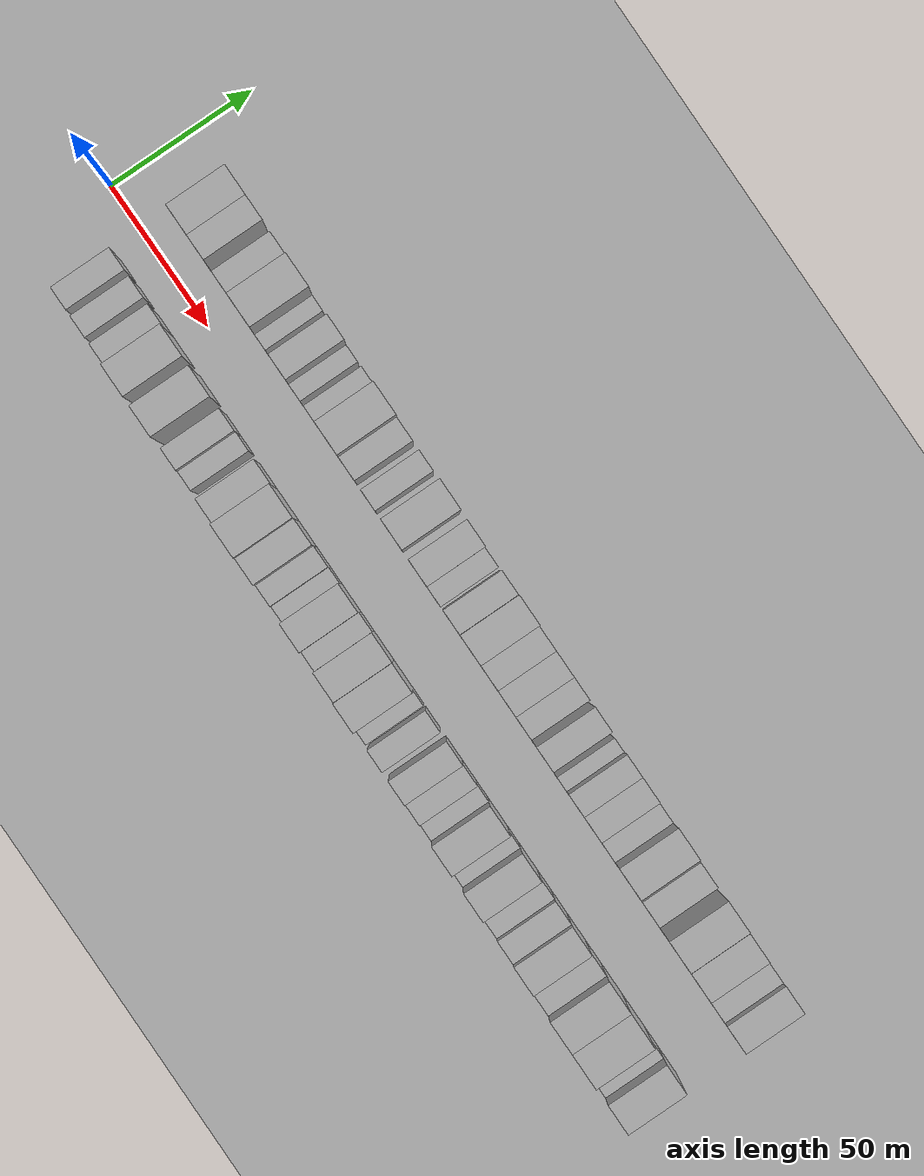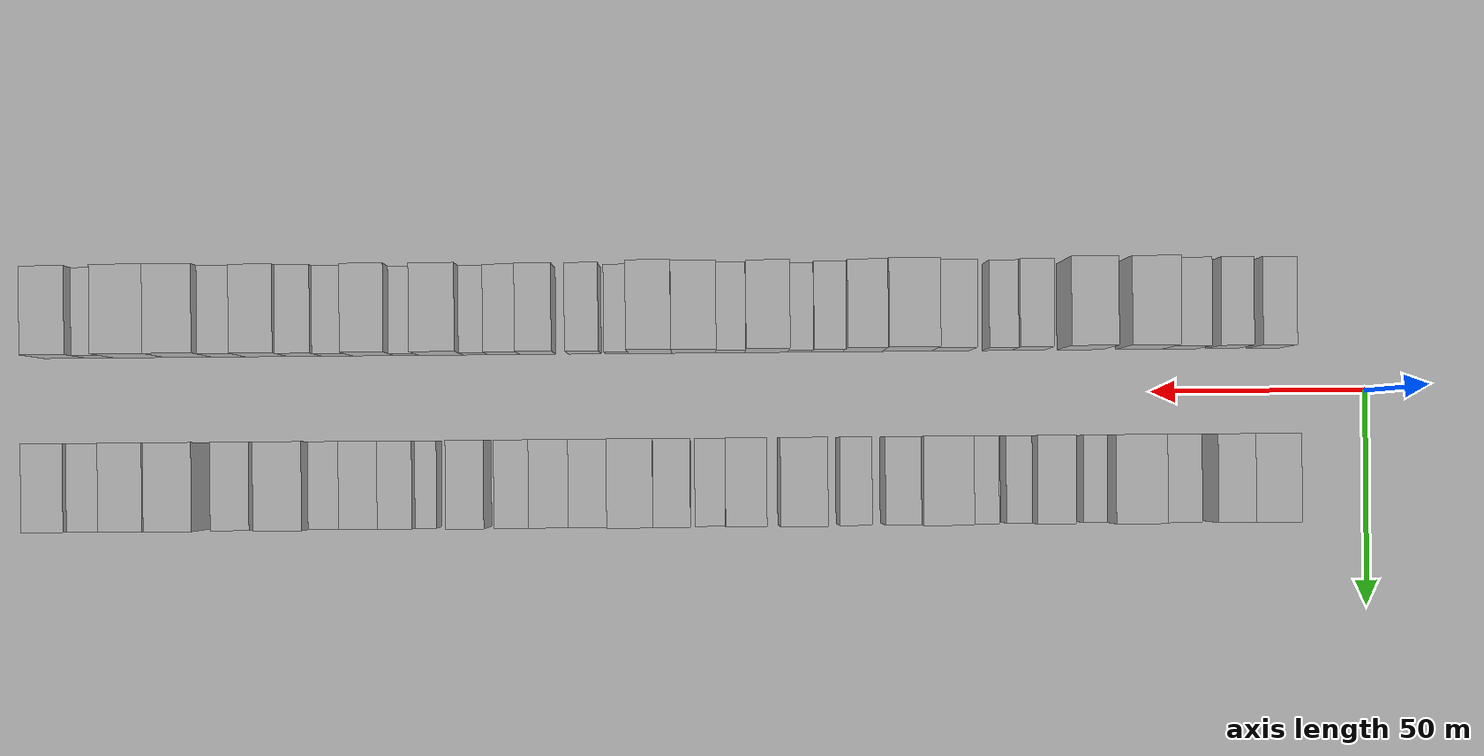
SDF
<?xml version="1.0" encoding="utf-8"?>

<sdf version="1.6">

   <world name="default">

      <gui fullscreen="0">

         <camera name="user_camera">

            <pose>-15 0 4.57585 0 0 0</pose>

            <view_controller>orbit</view_controller>

         </camera>

      </gui>

      <scene>

         <sky>

           <clouds>

             <speed>12</speed>

           </clouds>

         </sky>

         <ambient>0.4 0.4 0.4 1</ambient>

         <background>0.7 0.7 0.7 1</background>

         <shadows>1</shadows>

      </scene>

      <gravity>0 0 -9.8066</gravity>

      <magnetic_field>6e-06 2.3e-05 -4.2e-05</magnetic_field>

      <physics default="0" name="default_physics" type="ode">

         <ode>

            <solver>

               <type>quick</type>

               <iters>10</iters>

               <sor>1.0</sor>

               <use_dynamic_moi_rescaling>0</use_dynamic_moi_rescaling>

            </solver>

            <constraints>

               <cfm>0</cfm>

               <erp>0.2</erp>

               <contact_max_correcting_vel>100</contact_max_correcting_vel>

               <contact_surface_layer>0.001</contact_surface_layer>

            </constraints>

         </ode>

         <max_step_size>0.004</max_step_size>

         <real_time_factor>1</real_time_factor>

         <real_time_update_rate>250</real_time_update_rate>

      </physics>

      <light name="sun" type="directional">

         <cast_shadows>1</cast_shadows>

         <pose>0 0 10 0 0 0</pose>

         <diffuse>0.8 0.8 0.8 1</diffuse>

         <specular>0.2 0.2 0.2 1</specular>

         <attenuation>

            <range>1000</range>

            <constant>0.9</constant>

            <linear>0.01</linear>

            <quadratic>0.001</quadratic>

         </attenuation>

         <direction>-0.5 0.1 -0.9</direction>

      </light>

      <include>

         <name>ground_plane_1</name>

         <uri>model://HANNAS_ground_plane</uri>

         <pose>0 0 0  0 0 0</pose>

      </include>

      <include>

         <name>ground_plane_2</name>

         <uri>model://HANNAS_ground_plane</uri>

         <pose>100 0 0  0 0 0</pose>

      </include>

      <model name="building_1">

         <static>1</static>

         <pose frame="">25.1516 20.0000 0 0.000000 0.000000 1.570796</pose>

         <link name="link">

            <pose frame="">0 0 10.50 0 0 0</pose>

            <collision name="collision">

               <geometry>

                  <box>

                     <size>20.0000 10.3033 21.0000</size>

                  </box>

               </geometry>

               <max_contacts>10</max_contacts>

               <surface>

                  <contact>

                     <ode/>

                  </contact>

                  <bounce/>

                  <friction>

                     <torsional>

                        <ode/>

                     </torsional>

                     <ode/>

                  </friction>

               </surface>

            </collision>

            <visual name="visual">

               <cast_shadows>0</cast_shadows>

               <geometry>

                  <box>

                     <size>20.0000 10.3033 21.0000</size>

                  </box>

               </geometry>

               <material>

                  <script>

                     <uri>model://HANNAS_wall/materials/scripts</uri>

                     <uri>model://HANNAS_wall/materials/textures</uri>

                     <name>vrc/HANNAS_wall</name>

                  </script>

               </material>

            </visual>

            <self_collide>0</self_collide>

            <enable_wind>0</enable_wind>

            <kinematic>0</kinematic>

         </link>

      </model>

      <model name="building_2">

         <static>1</static>

         <pose frame="">34.5574 20.0000 0 0.000000 0.000000 1.570796</pose>

         <link name="link">

            <pose frame="">0 0 10.50 0 0 0</pose>

            <collision name="collision">

               <geometry>

                  <box>

                     <size>20.0000 8.5082 21.0000</size>

                  </box>

               </geometry>

               <max_contacts>10</max_contacts>

               <surface>

                  <contact>

                     <ode/>

                  </contact>

                  <bounce/>

                  <friction>

                     <torsional>

                        <ode/>

                     </torsional>

                     <ode/>

                  </friction>

               </surface>

            </collision>

            <visual name="visual">

               <cast_shadows>0</cast_shadows>

               <geometry>

                  <box>

                     <size>20.0000 8.5082 21.0000</size>

                  </box>

               </geometry>

               <material>

                  <script>

                     <uri>model://HANNAS_wall/materials/scripts</uri>

                     <uri>model://HANNAS_wall/materials/textures</uri>

                     <name>vrc/HANNAS_wall</name>

                  </script>

               </material>

            </visual>

            <self_collide>0</self_collide>

            <enable_wind>0</enable_wind>

            <kinematic>0</kinematic>

         </link>

      </model>

      <model name="building_3">

         <static>1</static>

         <pose frame="">46.2636 20.0000 0 0.000000 0.000000 1.570796</pose>

         <link name="link">

            <pose frame="">0 0 9.00 0 0 0</pose>

            <collision name="collision">

               <geometry>

                  <box>

                     <size>20.0000 8.9044 18.0000</size>

                  </box>

               </geometry>

               <max_contacts>10</max_contacts>

               <surface>

                  <contact>

                     <ode/>

                  </contact>

                  <bounce/>

                  <friction>

                     <torsional>

                        <ode/>

                     </torsional>

                     <ode/>

                  </friction>

               </surface>

            </collision>

            <visual name="visual">

               <cast_shadows>0</cast_shadows>

               <geometry>

                  <box>

                     <size>20.0000 8.9044 18.0000</size>

                  </box>

               </geometry>

               <material>

                  <script>

                     <uri>model://HANNAS_wall/materials/scripts</uri>

                     <uri>model://HANNAS_wall/materials/textures</uri>

                     <name>vrc/HANNAS_wall</name>

                  </script>

               </material>

            </visual>

            <self_collide>0</self_collide>

            <enable_wind>0</enable_wind>

            <kinematic>0</kinematic>

         </link>

      </model>

      <model name="building_4">

         <static>1</static>

         <pose frame="">56.4944 20.0000 0 0.000000 0.000000 1.570796</pose>

         <link name="link">

            <pose frame="">0 0 12.00 0 0 0</pose>

            <collision name="collision">

               <geometry>

                  <box>

                     <size>20.0000 11.5572 24.0000</size>

                  </box>

               </geometry>

               <max_contacts>10</max_contacts>

               <surface>

                  <contact>

                     <ode/>

                  </contact>

                  <bounce/>

                  <friction>

                     <torsional>

                        <ode/>

                     </torsional>

                     <ode/>

                  </friction>

               </surface>

            </collision>

            <visual name="visual">

               <cast_shadows>0</cast_shadows>

               <geometry>

                  <box>

                     <size>20.0000 11.5572 24.0000</size>

                  </box>

               </geometry>

               <material>

                  <script>

                     <uri>model://HANNAS_wall/materials/scripts</uri>

                     <uri>model://HANNAS_wall/materials/textures</uri>

                     <name>vrc/HANNAS_wall</name>

                  </script>

               </material>

            </visual>

            <self_collide>0</self_collide>

            <enable_wind>0</enable_wind>

            <kinematic>0</kinematic>

         </link>

      </model>

      <model name="building_5">

         <static>1</static>

         <pose frame="">65.0011 20.0000 0 0.000000 0.000000 1.570796</pose>

         <link name="link">

            <pose frame="">0 0 6.00 0 0 0</pose>

            <collision name="collision">

               <geometry>

                  <box>

                     <size>20.0000 5.4563 12.0000</size>

                  </box>

               </geometry>

               <max_contacts>10</max_contacts>

               <surface>

                  <contact>

                     <ode/>

                  </contact>

                  <bounce/>

                  <friction>

                     <torsional>

                        <ode/>

                     </torsional>

                     <ode/>

                  </friction>

               </surface>

            </collision>

            <visual name="visual">

               <cast_shadows>0</cast_shadows>

               <geometry>

                  <box>

                     <size>20.0000 5.4563 12.0000</size>

                  </box>

               </geometry>

               <material>

                  <script>

                     <uri>model://HANNAS_wall/materials/scripts</uri>

                     <uri>model://HANNAS_wall/materials/textures</uri>

                     <name>vrc/HANNAS_wall</name>

                  </script>

               </material>

            </visual>

            <self_collide>0</self_collide>

            <enable_wind>0</enable_wind>

            <kinematic>0</kinematic>

         </link>

      </model>

      <model name="building_6">

         <static>1</static>

         <pose frame="">75.0947 20.0000 0 0.000000 0.000000 1.570796</pose>

         <link name="link">

            <pose frame="">0 0 10.50 0 0 0</pose>

            <collision name="collision">

               <geometry>

                  <box>

                     <size>20.0000 8.7310 21.0000</size>

                  </box>

               </geometry>

               <max_contacts>10</max_contacts>

               <surface>

                  <contact>

                     <ode/>

                  </contact>

                  <bounce/>

                  <friction>

                     <torsional>

                        <ode/>

                     </torsional>

                     <ode/>

                  </friction>

               </surface>

            </collision>

            <visual name="visual">

               <cast_shadows>0</cast_shadows>

               <geometry>

                  <box>

                     <size>20.0000 8.7310 21.0000</size>

                  </box>

               </geometry>

               <material>

                  <script>

                     <uri>model://HANNAS_wall/materials/scripts</uri>

                     <uri>model://HANNAS_wall/materials/textures</uri>

                     <name>vrc/HANNAS_wall</name>

                  </script>

               </material>

            </visual>

            <self_collide>0</self_collide>

            <enable_wind>0</enable_wind>

            <kinematic>0</kinematic>

         </link>

      </model>

      <model name="building_7">

         <static>1</static>

         <pose frame="">82.4263 20.0000 0 0.000000 0.000000 1.570796</pose>

         <link name="link">

            <pose frame="">0 0 6.00 0 0 0</pose>

            <collision name="collision">

               <geometry>

                  <box>

                     <size>20.0000 5.9321 12.0000</size>

                  </box>

               </geometry>

               <max_contacts>10</max_contacts>

               <surface>

                  <contact>

                     <ode/>

                  </contact>

                  <bounce/>

                  <friction>

                     <torsional>

                        <ode/>

                     </torsional>

                     <ode/>

                  </friction>

               </surface>

            </collision>

            <visual name="visual">

               <cast_shadows>0</cast_shadows>

               <geometry>

                  <box>

                     <size>20.0000 5.9321 12.0000</size>

                  </box>

               </geometry>

               <material>

                  <script>

                     <uri>model://HANNAS_wall/materials/scripts</uri>

                     <uri>model://HANNAS_wall/materials/textures</uri>

                     <name>vrc/HANNAS_wall</name>

                  </script>

               </material>

            </visual>

            <self_collide>0</self_collide>

            <enable_wind>0</enable_wind>

            <kinematic>0</kinematic>

         </link>

      </model>

      <model name="building_8">

         <static>1</static>

         <pose frame="">90.7004 20.0000 0 0.000000 0.000000 1.570796</pose>

         <link name="link">

            <pose frame="">0 0 7.50 0 0 0</pose>

            <collision name="collision">

               <geometry>

                  <box>

                     <size>20.0000 6.6161 15.0000</size>

                  </box>

               </geometry>

               <max_contacts>10</max_contacts>

               <surface>

                  <contact>

                     <ode/>

                  </contact>

                  <bounce/>

                  <friction>

                     <torsional>

                        <ode/>

                     </torsional>

                     <ode/>

                  </friction>

               </surface>

            </collision>

            <visual name="visual">

               <cast_shadows>0</cast_shadows>

               <geometry>

                  <box>

                     <size>20.0000 6.6161 15.0000</size>

                  </box>

               </geometry>

               <material>

                  <script>

                     <uri>model://HANNAS_wall/materials/scripts</uri>

                     <uri>model://HANNAS_wall/materials/textures</uri>

                     <name>vrc/HANNAS_wall</name>

                  </script>

               </material>

            </visual>

            <self_collide>0</self_collide>

            <enable_wind>0</enable_wind>

            <kinematic>0</kinematic>

         </link>

      </model>

      <model name="building_9">

         <static>1</static>

         <pose frame="">99.6663 20.0000 0 0.000000 0.000000 1.570796</pose>

         <link name="link">

            <pose frame="">0 0 12.00 0 0 0</pose>

            <collision name="collision">

               <geometry>

                  <box>

                     <size>20.0000 11.3157 24.0000</size>

                  </box>

               </geometry>

               <max_contacts>10</max_contacts>

               <surface>

                  <contact>

                     <ode/>

                  </contact>

                  <bounce/>

                  <friction>

                     <torsional>

                        <ode/>

                     </torsional>

                     <ode/>

                  </friction>

               </surface>

            </collision>

            <visual name="visual">

               <cast_shadows>0</cast_shadows>

               <geometry>

                  <box>

                     <size>20.0000 11.3157 24.0000</size>

                  </box>

               </geometry>

               <material>

                  <script>

                     <uri>model://HANNAS_wall/materials/scripts</uri>

                     <uri>model://HANNAS_wall/materials/textures</uri>

                     <name>vrc/HANNAS_wall</name>

                  </script>

               </material>

            </visual>

            <self_collide>0</self_collide>

            <enable_wind>0</enable_wind>

            <kinematic>0</kinematic>

         </link>

      </model>

      <model name="building_10">

         <static>1</static>

         <pose frame="">109.3915 20.0000 0 0.000000 0.000000 1.570796</pose>

         <link name="link">

            <pose frame="">0 0 9.00 0 0 0</pose>

            <collision name="collision">

               <geometry>

                  <box>

                     <size>20.0000 8.1346 18.0000</size>

                  </box>

               </geometry>

               <max_contacts>10</max_contacts>

               <surface>

                  <contact>

                     <ode/>

                  </contact>

                  <bounce/>

                  <friction>

                     <torsional>

                        <ode/>

                     </torsional>

                     <ode/>

                  </friction>

               </surface>

            </collision>

            <visual name="visual">

               <cast_shadows>0</cast_shadows>

               <geometry>

                  <box>

                     <size>20.0000 8.1346 18.0000</size>

                  </box>

               </geometry>

               <material>

                  <script>

                     <uri>model://HANNAS_wall/materials/scripts</uri>

                     <uri>model://HANNAS_wall/materials/textures</uri>

                     <name>vrc/HANNAS_wall</name>

                  </script>

               </material>

            </visual>

            <self_collide>0</self_collide>

            <enable_wind>0</enable_wind>

            <kinematic>0</kinematic>

         </link>

      </model>

      <model name="building_11">

         <static>1</static>

         <pose frame="">120.1102 20.0000 0 0.000000 0.000000 1.570796</pose>

         <link name="link">

            <pose frame="">0 0 9.00 0 0 0</pose>

            <collision name="collision">

               <geometry>

                  <box>

                     <size>20.0000 7.3029 18.0000</size>

                  </box>

               </geometry>

               <max_contacts>10</max_contacts>

               <surface>

                  <contact>

                     <ode/>

                  </contact>

                  <bounce/>

                  <friction>

                     <torsional>

                        <ode/>

                     </torsional>

                     <ode/>

                  </friction>

               </surface>

            </collision>

            <visual name="visual">

               <cast_shadows>0</cast_shadows>

               <geometry>

                  <box>

                     <size>20.0000 7.3029 18.0000</size>

                  </box>

               </geometry>

               <material>

                  <script>

                     <uri>model://HANNAS_wall/materials/scripts</uri>

                     <uri>model://HANNAS_wall/materials/textures</uri>

                     <name>vrc/HANNAS_wall</name>

                  </script>

               </material>

            </visual>

            <self_collide>0</self_collide>

            <enable_wind>0</enable_wind>

            <kinematic>0</kinematic>

         </link>

      </model>

      <model name="building_12">

         <static>1</static>

         <pose frame="">132.0586 20.0000 0 0.000000 0.000000 1.570796</pose>

         <link name="link">

            <pose frame="">0 0 12.00 0 0 0</pose>

            <collision name="collision">

               <geometry>

                  <box>

                     <size>20.0000 10.5938 24.0000</size>

                  </box>

               </geometry>

               <max_contacts>10</max_contacts>

               <surface>

                  <contact>

                     <ode/>

                  </contact>

                  <bounce/>

                  <friction>

                     <torsional>

                        <ode/>

                     </torsional>

                     <ode/>

                  </friction>

               </surface>

            </collision>

            <visual name="visual">

               <cast_shadows>0</cast_shadows>

               <geometry>

                  <box>

                     <size>20.0000 10.5938 24.0000</size>

                  </box>

               </geometry>

               <material>

                  <script>

                     <uri>model://HANNAS_wall/materials/scripts</uri>

                     <uri>model://HANNAS_wall/materials/textures</uri>

                     <name>vrc/HANNAS_wall</name>

                  </script>

               </material>

            </visual>

            <self_collide>0</self_collide>

            <enable_wind>0</enable_wind>

            <kinematic>0</kinematic>

         </link>

      </model>

      <model name="building_13">

         <static>1</static>

         <pose frame="">145.0110 20.0000 0 0.000000 0.000000 1.570796</pose>

         <link name="link">

            <pose frame="">0 0 10.50 0 0 0</pose>

            <collision name="collision">

               <geometry>

                  <box>

                     <size>20.0000 9.3109 21.0000</size>

                  </box>

               </geometry>

               <max_contacts>10</max_contacts>

               <surface>

                  <contact>

                     <ode/>

                  </contact>

                  <bounce/>

                  <friction>

                     <torsional>

                        <ode/>

                     </torsional>

                     <ode/>

                  </friction>

               </surface>

            </collision>

            <visual name="visual">

               <cast_shadows>0</cast_shadows>

               <geometry>

                  <box>

                     <size>20.0000 9.3109 21.0000</size>

                  </box>

               </geometry>

               <material>

                  <script>

                     <uri>model://HANNAS_wall/materials/scripts</uri>

                     <uri>model://HANNAS_wall/materials/textures</uri>

                     <name>vrc/HANNAS_wall</name>

                  </script>

               </material>

            </visual>

            <self_collide>0</self_collide>

            <enable_wind>0</enable_wind>

            <kinematic>0</kinematic>

         </link>

      </model>

      <model name="building_14">

         <static>1</static>

         <pose frame="">153.1333 20.0000 0 0.000000 0.000000 1.570796</pose>

         <link name="link">

            <pose frame="">0 0 7.50 0 0 0</pose>

            <collision name="collision">

               <geometry>

                  <box>

                     <size>20.0000 6.9338 15.0000</size>

                  </box>

               </geometry>

               <max_contacts>10</max_contacts>

               <surface>

                  <contact>

                     <ode/>

                  </contact>

                  <bounce/>

                  <friction>

                     <torsional>

                        <ode/>

                     </torsional>

                     <ode/>

                  </friction>

               </surface>

            </collision>

            <visual name="visual">

               <cast_shadows>0</cast_shadows>

               <geometry>

                  <box>

                     <size>20.0000 6.9338 15.0000</size>

                  </box>

               </geometry>

               <material>

                  <script>

                     <uri>model://HANNAS_wall/materials/scripts</uri>

                     <uri>model://HANNAS_wall/materials/textures</uri>

                     <name>vrc/HANNAS_wall</name>

                  </script>

               </material>

            </visual>

            <self_collide>0</self_collide>

            <enable_wind>0</enable_wind>

            <kinematic>0</kinematic>

         </link>

      </model>

      <model name="building_15">

         <static>1</static>

         <pose frame="">161.8040 20.0000 0 0.000000 0.000000 1.570796</pose>

         <link name="link">

            <pose frame="">0 0 10.50 0 0 0</pose>

            <collision name="collision">

               <geometry>

                  <box>

                     <size>20.0000 8.4076 21.0000</size>

                  </box>

               </geometry>

               <max_contacts>10</max_contacts>

               <surface>

                  <contact>

                     <ode/>

                  </contact>

                  <bounce/>

                  <friction>

                     <torsional>

                        <ode/>

                     </torsional>

                     <ode/>

                  </friction>

               </surface>

            </collision>

            <visual name="visual">

               <cast_shadows>0</cast_shadows>

               <geometry>

                  <box>

                     <size>20.0000 8.4076 21.0000</size>

                  </box>

               </geometry>

               <material>

                  <script>

                     <uri>model://HANNAS_wall/materials/scripts</uri>

                     <uri>model://HANNAS_wall/materials/textures</uri>

                     <name>vrc/HANNAS_wall</name>

                  </script>

               </material>

            </visual>

            <self_collide>0</self_collide>

            <enable_wind>0</enable_wind>

            <kinematic>0</kinematic>

         </link>

      </model>

      <model name="building_16">

         <static>1</static>

         <pose frame="">171.1718 20.0000 0 0.000000 0.000000 1.570796</pose>

         <link name="link">

            <pose frame="">0 0 12.00 0 0 0</pose>

            <collision name="collision">

               <geometry>

                  <box>

                     <size>20.0000 10.3281 24.0000</size>

                  </box>

               </geometry>

               <max_contacts>10</max_contacts>

               <surface>

                  <contact>

                     <ode/>

                  </contact>

                  <bounce/>

                  <friction>

                     <torsional>

                        <ode/>

                     </torsional>

                     <ode/>

                  </friction>

               </surface>

            </collision>

            <visual name="visual">

               <cast_shadows>0</cast_shadows>

               <geometry>

                  <box>

                     <size>20.0000 10.3281 24.0000</size>

                  </box>

               </geometry>

               <material>

                  <script>

                     <uri>model://HANNAS_wall/materials/scripts</uri>

                     <uri>model://HANNAS_wall/materials/textures</uri>

                     <name>vrc/HANNAS_wall</name>

                  </script>

               </material>

            </visual>

            <self_collide>0</self_collide>

            <enable_wind>0</enable_wind>

            <kinematic>0</kinematic>

         </link>

      </model>

      <model name="building_17">

         <static>1</static>

         <pose frame="">180.7952 20.0000 0 0.000000 0.000000 1.570796</pose>

         <link name="link">

            <pose frame="">0 0 9.00 0 0 0</pose>

            <collision name="collision">

               <geometry>

                  <box>

                     <size>20.0000 8.9186 18.0000</size>

                  </box>

               </geometry>

               <max_contacts>10</max_contacts>

               <surface>

                  <contact>

                     <ode/>

                  </contact>

                  <bounce/>

                  <friction>

                     <torsional>

                        <ode/>

                     </torsional>

                     <ode/>

                  </friction>

               </surface>

            </collision>

            <visual name="visual">

               <cast_shadows>0</cast_shadows>

               <geometry>

                  <box>

                     <size>20.0000 8.9186 18.0000</size>

                  </box>

               </geometry>

               <material>

                  <script>

                     <uri>model://HANNAS_wall/materials/scripts</uri>

                     <uri>model://HANNAS_wall/materials/textures</uri>

                     <name>vrc/HANNAS_wall</name>

                  </script>

               </material>

            </visual>

            <self_collide>0</self_collide>

            <enable_wind>0</enable_wind>

            <kinematic>0</kinematic>

         </link>

      </model>

      <model name="building_18">

         <static>1</static>

         <pose frame="">189.7408 20.0000 0 0.000000 0.000000 1.570796</pose>

         <link name="link">

            <pose frame="">0 0 9.00 0 0 0</pose>

            <collision name="collision">

               <geometry>

                  <box>

                     <size>20.0000 8.9726 18.0000</size>

                  </box>

               </geometry>

               <max_contacts>10</max_contacts>

               <surface>

                  <contact>

                     <ode/>

                  </contact>

                  <bounce/>

                  <friction>

                     <torsional>

                        <ode/>

                     </torsional>

                     <ode/>

                  </friction>

               </surface>

            </collision>

            <visual name="visual">

               <cast_shadows>0</cast_shadows>

               <geometry>

                  <box>

                     <size>20.0000 8.9726 18.0000</size>

                  </box>

               </geometry>

               <material>

                  <script>

                     <uri>model://HANNAS_wall/materials/scripts</uri>

                     <uri>model://HANNAS_wall/materials/textures</uri>

                     <name>vrc/HANNAS_wall</name>

                  </script>

               </material>

            </visual>

            <self_collide>0</self_collide>

            <enable_wind>0</enable_wind>

            <kinematic>0</kinematic>

         </link>

      </model>

      <model name="building_19">

         <static>1</static>

         <pose frame="">198.1437 20.0000 0 0.000000 0.000000 1.570796</pose>

         <link name="link">

            <pose frame="">0 0 9.00 0 0 0</pose>

            <collision name="collision">

               <geometry>

                  <box>

                     <size>20.0000 7.8333 18.0000</size>

                  </box>

               </geometry>

               <max_contacts>10</max_contacts>

               <surface>

                  <contact>

                     <ode/>

                  </contact>

                  <bounce/>

                  <friction>

                     <torsional>

                        <ode/>

                     </torsional>

                     <ode/>

                  </friction>

               </surface>

            </collision>

            <visual name="visual">

               <cast_shadows>0</cast_shadows>

               <geometry>

                  <box>

                     <size>20.0000 7.8333 18.0000</size>

                  </box>

               </geometry>

               <material>

                  <script>

                     <uri>model://HANNAS_wall/materials/scripts</uri>

                     <uri>model://HANNAS_wall/materials/textures</uri>

                     <name>vrc/HANNAS_wall</name>

                  </script>

               </material>

            </visual>

            <self_collide>0</self_collide>

            <enable_wind>0</enable_wind>

            <kinematic>0</kinematic>

         </link>

      </model>

      <model name="building_20">

         <static>1</static>

         <pose frame="">208.3549 20.0000 0 0.000000 0.000000 1.570796</pose>

         <link name="link">

            <pose frame="">0 0 10.50 0 0 0</pose>

            <collision name="collision">

               <geometry>

                  <box>

                     <size>20.0000 8.5891 21.0000</size>

                  </box>

               </geometry>

               <max_contacts>10</max_contacts>

               <surface>

                  <contact>

                     <ode/>

                  </contact>

                  <bounce/>

                  <friction>

                     <torsional>

                        <ode/>

                     </torsional>

                     <ode/>

                  </friction>

               </surface>

            </collision>

            <visual name="visual">

               <cast_shadows>0</cast_shadows>

               <geometry>

                  <box>

                     <size>20.0000 8.5891 21.0000</size>

                  </box>

               </geometry>

               <material>

                  <script>

                     <uri>model://HANNAS_wall/materials/scripts</uri>

                     <uri>model://HANNAS_wall/materials/textures</uri>

                     <name>vrc/HANNAS_wall</name>

                  </script>

               </material>

            </visual>

            <self_collide>0</self_collide>

            <enable_wind>0</enable_wind>

            <kinematic>0</kinematic>

         </link>

      </model>

      <model name="building_21">

         <static>1</static>

         <pose frame="">218.1163 20.0000 0 0.000000 0.000000 1.570796</pose>

         <link name="link">

            <pose frame="">0 0 6.00 0 0 0</pose>

            <collision name="collision">

               <geometry>

                  <box>

                     <size>20.0000 4.9337 12.0000</size>

                  </box>

               </geometry>

               <max_contacts>10</max_contacts>

               <surface>

                  <contact>

                     <ode/>

                  </contact>

                  <bounce/>

                  <friction>

                     <torsional>

                        <ode/>

                     </torsional>

                     <ode/>

                  </friction>

               </surface>

            </collision>

            <visual name="visual">

               <cast_shadows>0</cast_shadows>

               <geometry>

                  <box>

                     <size>20.0000 4.9337 12.0000</size>

                  </box>

               </geometry>

               <material>

                  <script>

                     <uri>model://HANNAS_wall/materials/scripts</uri>

                     <uri>model://HANNAS_wall/materials/textures</uri>

                     <name>vrc/HANNAS_wall</name>

                  </script>

               </material>

            </visual>

            <self_collide>0</self_collide>

            <enable_wind>0</enable_wind>

            <kinematic>0</kinematic>

         </link>

      </model>

      <model name="building_22">

         <static>1</static>

         <pose frame="">224.5152 20.0000 0 0.000000 0.000000 1.570796</pose>

         <link name="link">

            <pose frame="">0 0 9.00 0 0 0</pose>

            <collision name="collision">

               <geometry>

                  <box>

                     <size>20.0000 7.8642 18.0000</size>

                  </box>

               </geometry>

               <max_contacts>10</max_contacts>

               <surface>

                  <contact>

                     <ode/>

                  </contact>

                  <bounce/>

                  <friction>

                     <torsional>

                        <ode/>

                     </torsional>

                     <ode/>

                  </friction>

               </surface>

            </collision>

            <visual name="visual">

               <cast_shadows>0</cast_shadows>

               <geometry>

                  <box>

                     <size>20.0000 7.8642 18.0000</size>

                  </box>

               </geometry>

               <material>

                  <script>

                     <uri>model://HANNAS_wall/materials/scripts</uri>

                     <uri>model://HANNAS_wall/materials/textures</uri>

                     <name>vrc/HANNAS_wall</name>

                  </script>

               </material>

            </visual>

            <self_collide>0</self_collide>

            <enable_wind>0</enable_wind>

            <kinematic>0</kinematic>

         </link>

      </model>

      <model name="building_23">

         <static>1</static>

         <pose frame="">232.8145 20.0000 0 0.000000 0.000000 1.570796</pose>

         <link name="link">

            <pose frame="">0 0 9.00 0 0 0</pose>

            <collision name="collision">

               <geometry>

                  <box>

                     <size>20.0000 8.7344 18.0000</size>

                  </box>

               </geometry>

               <max_contacts>10</max_contacts>

               <surface>

                  <contact>

                     <ode/>

                  </contact>

                  <bounce/>

                  <friction>

                     <torsional>

                        <ode/>

                     </torsional>

                     <ode/>

                  </friction>

               </surface>

            </collision>

            <visual name="visual">

               <cast_shadows>0</cast_shadows>

               <geometry>

                  <box>

                     <size>20.0000 8.7344 18.0000</size>

                  </box>

               </geometry>

               <material>

                  <script>

                     <uri>model://HANNAS_wall/materials/scripts</uri>

                     <uri>model://HANNAS_wall/materials/textures</uri>

                     <name>vrc/HANNAS_wall</name>

                  </script>

               </material>

            </visual>

            <self_collide>0</self_collide>

            <enable_wind>0</enable_wind>

            <kinematic>0</kinematic>

         </link>

      </model>

      <model name="building_24">

         <static>1</static>

         <pose frame="">240.8632 20.0000 0 0.000000 0.000000 1.570796</pose>

         <link name="link">

            <pose frame="">0 0 7.50 0 0 0</pose>

            <collision name="collision">

               <geometry>

                  <box>

                     <size>20.0000 7.3629 15.0000</size>

                  </box>

               </geometry>

               <max_contacts>10</max_contacts>

               <surface>

                  <contact>

                     <ode/>

                  </contact>

                  <bounce/>

                  <friction>

                     <torsional>

                        <ode/>

                     </torsional>

                     <ode/>

                  </friction>

               </surface>

            </collision>

            <visual name="visual">

               <cast_shadows>0</cast_shadows>

               <geometry>

                  <box>

                     <size>20.0000 7.3629 15.0000</size>

                  </box>

               </geometry>

               <material>

                  <script>

                     <uri>model://HANNAS_wall/materials/scripts</uri>

                     <uri>model://HANNAS_wall/materials/textures</uri>

                     <name>vrc/HANNAS_wall</name>

                  </script>

               </material>

            </visual>

            <self_collide>0</self_collide>

            <enable_wind>0</enable_wind>

            <kinematic>0</kinematic>

         </link>

      </model>

      <model name="building_25">

         <static>1</static>

         <pose frame="">249.9842 20.0000 0 0.000000 0.000000 1.570796</pose>

         <link name="link">

            <pose frame="">0 0 12.00 0 0 0</pose>

            <collision name="collision">

               <geometry>

                  <box>

                     <size>20.0000 10.8793 24.0000</size>

                  </box>

               </geometry>

               <max_contacts>10</max_contacts>

               <surface>

                  <contact>

                     <ode/>

                  </contact>

                  <bounce/>

                  <friction>

                     <torsional>

                        <ode/>

                     </torsional>

                     <ode/>

                  </friction>

               </surface>

            </collision>

            <visual name="visual">

               <cast_shadows>0</cast_shadows>

               <geometry>

                  <box>

                     <size>20.0000 10.8793 24.0000</size>

                  </box>

               </geometry>

               <material>

                  <script>

                     <uri>model://HANNAS_wall/materials/scripts</uri>

                     <uri>model://HANNAS_wall/materials/textures</uri>

                     <name>vrc/HANNAS_wall</name>

                  </script>

               </material>

            </visual>

            <self_collide>0</self_collide>

            <enable_wind>0</enable_wind>

            <kinematic>0</kinematic>

         </link>

      </model>

      <model name="building_26">

         <static>1</static>

         <pose frame="">261.8048 20.0000 0 0.000000 0.000000 1.570796</pose>

         <link name="link">

            <pose frame="">0 0 9.00 0 0 0</pose>

            <collision name="collision">

               <geometry>

                  <box>

                     <size>20.0000 8.7619 18.0000</size>

                  </box>

               </geometry>

               <max_contacts>10</max_contacts>

               <surface>

                  <contact>

                     <ode/>

                  </contact>

                  <bounce/>

                  <friction>

                     <torsional>

                        <ode/>

                     </torsional>

                     <ode/>

                  </friction>

               </surface>

            </collision>

            <visual name="visual">

               <cast_shadows>0</cast_shadows>

               <geometry>

                  <box>

                     <size>20.0000 8.7619 18.0000</size>

                  </box>

               </geometry>

               <material>

                  <script>

                     <uri>model://HANNAS_wall/materials/scripts</uri>

                     <uri>model://HANNAS_wall/materials/textures</uri>

                     <name>vrc/HANNAS_wall</name>

                  </script>

               </material>

            </visual>

            <self_collide>0</self_collide>

            <enable_wind>0</enable_wind>

            <kinematic>0</kinematic>

         </link>

      </model>

      <model name="building_27">

         <static>1</static>

         <pose frame="">274.5712 20.0000 0 0.000000 0.000000 1.570796</pose>

         <link name="link">

            <pose frame="">0 0 12.00 0 0 0</pose>

            <collision name="collision">

               <geometry>

                  <box>

                     <size>20.0000 10.7709 24.0000</size>

                  </box>

               </geometry>

               <max_contacts>10</max_contacts>

               <surface>

                  <contact>

                     <ode/>

                  </contact>

                  <bounce/>

                  <friction>

                     <torsional>

                        <ode/>

                     </torsional>

                     <ode/>

                  </friction>

               </surface>

            </collision>

            <visual name="visual">

               <cast_shadows>0</cast_shadows>

               <geometry>

                  <box>

                     <size>20.0000 10.7709 24.0000</size>

                  </box>

               </geometry>

               <material>

                  <script>

                     <uri>model://HANNAS_wall/materials/scripts</uri>

                     <uri>model://HANNAS_wall/materials/textures</uri>

                     <name>vrc/HANNAS_wall</name>

                  </script>

               </material>

            </visual>

            <self_collide>0</self_collide>

            <enable_wind>0</enable_wind>

            <kinematic>0</kinematic>

         </link>

      </model>

      <model name="building_28">

         <static>1</static>

         <pose frame="">285.9206 20.0000 0 0.000000 0.000000 1.570796</pose>

         <link name="link">

            <pose frame="">0 0 10.50 0 0 0</pose>

            <collision name="collision">

               <geometry>

                  <box>

                     <size>20.0000 9.9280 21.0000</size>

                  </box>

               </geometry>

               <max_contacts>10</max_contacts>

               <surface>

                  <contact>

                     <ode/>

                  </contact>

                  <bounce/>

                  <friction>

                     <torsional>

                        <ode/>

                     </torsional>

                     <ode/>

                  </friction>

               </surface>

            </collision>

            <visual name="visual">

               <cast_shadows>0</cast_shadows>

               <geometry>

                  <box>

                     <size>20.0000 9.9280 21.0000</size>

                  </box>

               </geometry>

               <material>

                  <script>

                     <uri>model://HANNAS_wall/materials/scripts</uri>

                     <uri>model://HANNAS_wall/materials/textures</uri>

                     <name>vrc/HANNAS_wall</name>

                  </script>

               </material>

            </visual>

            <self_collide>0</self_collide>

            <enable_wind>0</enable_wind>

            <kinematic>0</kinematic>

         </link>

      </model>

      <model name="building_29">

         <static>1</static>

         <pose frame="">294.7935 20.0000 0 0.000000 0.000000 1.570796</pose>

         <link name="link">

            <pose frame="">0 0 9.00 0 0 0</pose>

            <collision name="collision">

               <geometry>

                  <box>

                     <size>20.0000 7.8178 18.0000</size>

                  </box>

               </geometry>

               <max_contacts>10</max_contacts>

               <surface>

                  <contact>

                     <ode/>

                  </contact>

                  <bounce/>

                  <friction>

                     <torsional>

                        <ode/>

                     </torsional>

                     <ode/>

                  </friction>

               </surface>

            </collision>

            <visual name="visual">

               <cast_shadows>0</cast_shadows>

               <geometry>

                  <box>

                     <size>20.0000 7.8178 18.0000</size>

                  </box>

               </geometry>

               <material>

                  <script>

                     <uri>model://HANNAS_wall/materials/scripts</uri>

                     <uri>model://HANNAS_wall/materials/textures</uri>

                     <name>vrc/HANNAS_wall</name>

                  </script>

               </material>

            </visual>

            <self_collide>0</self_collide>

            <enable_wind>0</enable_wind>

            <kinematic>0</kinematic>

         </link>

      </model>

      <model name="building_30">

         <static>1</static>

         <pose frame="">303.4305 20.0000 0 0.000000 0.000000 1.570796</pose>

         <link name="link">

            <pose frame="">0 0 10.50 0 0 0</pose>

            <collision name="collision">

               <geometry>

                  <box>

                     <size>20.0000 9.4562 21.0000</size>

                  </box>

               </geometry>

               <max_contacts>10</max_contacts>

               <surface>

                  <contact>

                     <ode/>

                  </contact>

                  <bounce/>

                  <friction>

                     <torsional>

                        <ode/>

                     </torsional>

                     <ode/>

                  </friction>

               </surface>

            </collision>

            <visual name="visual">

               <cast_shadows>0</cast_shadows>

               <geometry>

                  <box>

                     <size>20.0000 9.4562 21.0000</size>

                  </box>

               </geometry>

               <material>

                  <script>

                     <uri>model://HANNAS_wall/materials/scripts</uri>

                     <uri>model://HANNAS_wall/materials/textures</uri>

                     <name>vrc/HANNAS_wall</name>

                  </script>

               </material>

            </visual>

            <self_collide>0</self_collide>

            <enable_wind>0</enable_wind>

            <kinematic>0</kinematic>

         </link>

      </model>

      <model name="building_31">

         <static>1</static>

         <pose frame="">23.8754 -20.0000 0 0.000000 0.000000 1.570796</pose>

         <link name="link">

            <pose frame="">0 0 9.00 0 0 0</pose>

            <collision name="collision">

               <geometry>

                  <box>

                     <size>20.0000 7.7508 18.0000</size>

                  </box>

               </geometry>

               <max_contacts>10</max_contacts>

               <surface>

                  <contact>

                     <ode/>

                  </contact>

                  <bounce/>

                  <friction>

                     <torsional>

                        <ode/>

                     </torsional>

                     <ode/>

                  </friction>

               </surface>

            </collision>

            <visual name="visual">

               <cast_shadows>0</cast_shadows>

               <geometry>

                  <box>

                     <size>20.0000 7.7508 18.0000</size>

                  </box>

               </geometry>

               <material>

                  <script>

                     <uri>model://HANNAS_wall/materials/scripts</uri>

                     <uri>model://HANNAS_wall/materials/textures</uri>

                     <name>vrc/HANNAS_wall</name>

                  </script>

               </material>

            </visual>

            <self_collide>0</self_collide>

            <enable_wind>0</enable_wind>

            <kinematic>0</kinematic>

         </link>

      </model>

      <model name="building_32">

         <static>1</static>

         <pose frame="">33.4830 -20.0000 0 0.000000 0.000000 1.570796</pose>

         <link name="link">

            <pose frame="">0 0 9.00 0 0 0</pose>

            <collision name="collision">

               <geometry>

                  <box>

                     <size>20.0000 7.4644 18.0000</size>

                  </box>

               </geometry>

               <max_contacts>10</max_contacts>

               <surface>

                  <contact>

                     <ode/>

                  </contact>

                  <bounce/>

                  <friction>

                     <torsional>

                        <ode/>

                     </torsional>

                     <ode/>

                  </friction>

               </surface>

            </collision>

            <visual name="visual">

               <cast_shadows>0</cast_shadows>

               <geometry>

                  <box>

                     <size>20.0000 7.4644 18.0000</size>

                  </box>

               </geometry>

               <material>

                  <script>

                     <uri>model://HANNAS_wall/materials/scripts</uri>

                     <uri>model://HANNAS_wall/materials/textures</uri>

                     <name>vrc/HANNAS_wall</name>

                  </script>

               </material>

            </visual>

            <self_collide>0</self_collide>

            <enable_wind>0</enable_wind>

            <kinematic>0</kinematic>

         </link>

      </model>

      <model name="building_33">

         <static>1</static>

         <pose frame="">43.2879 -20.0000 0 0.000000 0.000000 1.570796</pose>

         <link name="link">

            <pose frame="">0 0 9.00 0 0 0</pose>

            <collision name="collision">

               <geometry>

                  <box>

                     <size>20.0000 8.1454 18.0000</size>

                  </box>

               </geometry>

               <max_contacts>10</max_contacts>

               <surface>

                  <contact>

                     <ode/>

                  </contact>

                  <bounce/>

                  <friction>

                     <torsional>

                        <ode/>

                     </torsional>

                     <ode/>

                  </friction>

               </surface>

            </collision>

            <visual name="visual">

               <cast_shadows>0</cast_shadows>

               <geometry>

                  <box>

                     <size>20.0000 8.1454 18.0000</size>

                  </box>

               </geometry>

               <material>

                  <script>

                     <uri>model://HANNAS_wall/materials/scripts</uri>

                     <uri>model://HANNAS_wall/materials/textures</uri>

                     <name>vrc/HANNAS_wall</name>

                  </script>

               </material>

            </visual>

            <self_collide>0</self_collide>

            <enable_wind>0</enable_wind>

            <kinematic>0</kinematic>

         </link>

      </model>

      <model name="building_34">

         <static>1</static>

         <pose frame="">52.8335 -20.0000 0 0.000000 0.000000 1.570796</pose>

         <link name="link">

            <pose frame="">0 0 12.00 0 0 0</pose>

            <collision name="collision">

               <geometry>

                  <box>

                     <size>20.0000 10.9457 24.0000</size>

                  </box>

               </geometry>

               <max_contacts>10</max_contacts>

               <surface>

                  <contact>

                     <ode/>

                  </contact>

                  <bounce/>

                  <friction>

                     <torsional>

                        <ode/>

                     </torsional>

                     <ode/>

                  </friction>

               </surface>

            </collision>

            <visual name="visual">

               <cast_shadows>0</cast_shadows>

               <geometry>

                  <box>

                     <size>20.0000 10.9457 24.0000</size>

                  </box>

               </geometry>

               <material>

                  <script>

                     <uri>model://HANNAS_wall/materials/scripts</uri>

                     <uri>model://HANNAS_wall/materials/textures</uri>

                     <name>vrc/HANNAS_wall</name>

                  </script>

               </material>

            </visual>

            <self_collide>0</self_collide>

            <enable_wind>0</enable_wind>

            <kinematic>0</kinematic>

         </link>

      </model>

      <model name="building_35">

         <static>1</static>

         <pose frame="">66.6143 -20.0000 0 0.000000 0.000000 1.570796</pose>

         <link name="link">

            <pose frame="">0 0 12.00 0 0 0</pose>

            <collision name="collision">

               <geometry>

                  <box>

                     <size>20.0000 10.6161 24.0000</size>

                  </box>

               </geometry>

               <max_contacts>10</max_contacts>

               <surface>

                  <contact>

                     <ode/>

                  </contact>

                  <bounce/>

                  <friction>

                     <torsional>

                        <ode/>

                     </torsional>

                     <ode/>

                  </friction>

               </surface>

            </collision>

            <visual name="visual">

               <cast_shadows>0</cast_shadows>

               <geometry>

                  <box>

                     <size>20.0000 10.6161 24.0000</size>

                  </box>

               </geometry>

               <material>

                  <script>

                     <uri>model://HANNAS_wall/materials/scripts</uri>

                     <uri>model://HANNAS_wall/materials/textures</uri>

                     <name>vrc/HANNAS_wall</name>

                  </script>

               </material>

            </visual>

            <self_collide>0</self_collide>

            <enable_wind>0</enable_wind>

            <kinematic>0</kinematic>

         </link>

      </model>

      <model name="building_36">

         <static>1</static>

         <pose frame="">78.7757 -20.0000 0 0.000000 0.000000 1.570796</pose>

         <link name="link">

            <pose frame="">0 0 9.00 0 0 0</pose>

            <collision name="collision">

               <geometry>

                  <box>

                     <size>20.0000 7.7067 18.0000</size>

                  </box>

               </geometry>

               <max_contacts>10</max_contacts>

               <surface>

                  <contact>

                     <ode/>

                  </contact>

                  <bounce/>

                  <friction>

                     <torsional>

                        <ode/>

                     </torsional>

                     <ode/>

                  </friction>

               </surface>

            </collision>

            <visual name="visual">

               <cast_shadows>0</cast_shadows>

               <geometry>

                  <box>

                     <size>20.0000 7.7067 18.0000</size>

                  </box>

               </geometry>

               <material>

                  <script>

                     <uri>model://HANNAS_wall/materials/scripts</uri>

                     <uri>model://HANNAS_wall/materials/textures</uri>

                     <name>vrc/HANNAS_wall</name>

                  </script>

               </material>

            </visual>

            <self_collide>0</self_collide>

            <enable_wind>0</enable_wind>

            <kinematic>0</kinematic>

         </link>

      </model>

      <model name="building_37">

         <static>1</static>

         <pose frame="">85.9521 -20.0000 0 0.000000 0.000000 1.570796</pose>

         <link name="link">

            <pose frame="">0 0 7.50 0 0 0</pose>

            <collision name="collision">

               <geometry>

                  <box>

                     <size>20.0000 6.6461 15.0000</size>

                  </box>

               </geometry>

               <max_contacts>10</max_contacts>

               <surface>

                  <contact>

                     <ode/>

                  </contact>

                  <bounce/>

                  <friction>

                     <torsional>

                        <ode/>

                     </torsional>

                     <ode/>

                  </friction>

               </surface>

            </collision>

            <visual name="visual">

               <cast_shadows>0</cast_shadows>

               <geometry>

                  <box>

                     <size>20.0000 6.6461 15.0000</size>

                  </box>

               </geometry>

               <material>

                  <script>

                     <uri>model://HANNAS_wall/materials/scripts</uri>

                     <uri>model://HANNAS_wall/materials/textures</uri>

                     <name>vrc/HANNAS_wall</name>

                  </script>

               </material>

            </visual>

            <self_collide>0</self_collide>

            <enable_wind>0</enable_wind>

            <kinematic>0</kinematic>

         </link>

      </model>

      <model name="building_38">

         <static>1</static>

         <pose frame="">96.7349 -20.0000 0 0.000000 0.000000 1.570796</pose>

         <link name="link">

            <pose frame="">0 0 9.00 0 0 0</pose>

            <collision name="collision">

               <geometry>

                  <box>

                     <size>20.0000 8.9194 18.0000</size>

                  </box>

               </geometry>

               <max_contacts>10</max_contacts>

               <surface>

                  <contact>

                     <ode/>

                  </contact>

                  <bounce/>

                  <friction>

                     <torsional>

                        <ode/>

                     </torsional>

                     <ode/>

                  </friction>

               </surface>

            </collision>

            <visual name="visual">

               <cast_shadows>0</cast_shadows>

               <geometry>

                  <box>

                     <size>20.0000 8.9194 18.0000</size>

                  </box>

               </geometry>

               <material>

                  <script>

                     <uri>model://HANNAS_wall/materials/scripts</uri>

                     <uri>model://HANNAS_wall/materials/textures</uri>

                     <name>vrc/HANNAS_wall</name>

                  </script>

               </material>

            </visual>

            <self_collide>0</self_collide>

            <enable_wind>0</enable_wind>

            <kinematic>0</kinematic>

         </link>

      </model>

      <model name="building_39">

         <static>1</static>

         <pose frame="">106.9634 -20.0000 0 0.000000 0.000000 1.570796</pose>

         <link name="link">

            <pose frame="">0 0 12.00 0 0 0</pose>

            <collision name="collision">

               <geometry>

                  <box>

                     <size>20.0000 11.5376 24.0000</size>

                  </box>

               </geometry>

               <max_contacts>10</max_contacts>

               <surface>

                  <contact>

                     <ode/>

                  </contact>

                  <bounce/>

                  <friction>

                     <torsional>

                        <ode/>

                     </torsional>

                     <ode/>

                  </friction>

               </surface>

            </collision>

            <visual name="visual">

               <cast_shadows>0</cast_shadows>

               <geometry>

                  <box>

                     <size>20.0000 11.5376 24.0000</size>

                  </box>

               </geometry>

               <material>

                  <script>

                     <uri>model://HANNAS_wall/materials/scripts</uri>

                     <uri>model://HANNAS_wall/materials/textures</uri>

                     <name>vrc/HANNAS_wall</name>

                  </script>

               </material>

            </visual>

            <self_collide>0</self_collide>

            <enable_wind>0</enable_wind>

            <kinematic>0</kinematic>

         </link>

      </model>

      <model name="building_40">

         <static>1</static>

         <pose frame="">117.2885 -20.0000 0 0.000000 0.000000 1.570796</pose>

         <link name="link">

            <pose frame="">0 0 10.50 0 0 0</pose>

            <collision name="collision">

               <geometry>

                  <box>

                     <size>20.0000 9.1125 21.0000</size>

                  </box>

               </geometry>

               <max_contacts>10</max_contacts>

               <surface>

                  <contact>

                     <ode/>

                  </contact>

                  <bounce/>

                  <friction>

                     <torsional>

                        <ode/>

                     </torsional>

                     <ode/>

                  </friction>

               </surface>

            </collision>

            <visual name="visual">

               <cast_shadows>0</cast_shadows>

               <geometry>

                  <box>

                     <size>20.0000 9.1125 21.0000</size>

                  </box>

               </geometry>

               <material>

                  <script>

                     <uri>model://HANNAS_wall/materials/scripts</uri>

                     <uri>model://HANNAS_wall/materials/textures</uri>

                     <name>vrc/HANNAS_wall</name>

                  </script>

               </material>

            </visual>

            <self_collide>0</self_collide>

            <enable_wind>0</enable_wind>

            <kinematic>0</kinematic>

         </link>

      </model>

      <model name="building_41">

         <static>1</static>

         <pose frame="">125.5029 -20.0000 0 0.000000 0.000000 1.570796</pose>

         <link name="link">

            <pose frame="">0 0 7.50 0 0 0</pose>

            <collision name="collision">

               <geometry>

                  <box>

                     <size>20.0000 7.3164 15.0000</size>

                  </box>

               </geometry>

               <max_contacts>10</max_contacts>

               <surface>

                  <contact>

                     <ode/>

                  </contact>

                  <bounce/>

                  <friction>

                     <torsional>

                        <ode/>

                     </torsional>

                     <ode/>

                  </friction>

               </surface>

            </collision>

            <visual name="visual">

               <cast_shadows>0</cast_shadows>

               <geometry>

                  <box>

                     <size>20.0000 7.3164 15.0000</size>

                  </box>

               </geometry>

               <material>

                  <script>

                     <uri>model://HANNAS_wall/materials/scripts</uri>

                     <uri>model://HANNAS_wall/materials/textures</uri>

                     <name>vrc/HANNAS_wall</name>

                  </script>

               </material>

            </visual>

            <self_collide>0</self_collide>

            <enable_wind>0</enable_wind>

            <kinematic>0</kinematic>

         </link>

      </model>

      <model name="building_42">

         <static>1</static>

         <pose frame="">131.9861 -20.0000 0 0.000000 0.000000 1.570796</pose>

         <link name="link">

            <pose frame="">0 0 6.00 0 0 0</pose>

            <collision name="collision">

               <geometry>

                  <box>

                     <size>20.0000 5.6499 12.0000</size>

                  </box>

               </geometry>

               <max_contacts>10</max_contacts>

               <surface>

                  <contact>

                     <ode/>

                  </contact>

                  <bounce/>

                  <friction>

                     <torsional>

                        <ode/>

                     </torsional>

                     <ode/>

                  </friction>

               </surface>

            </collision>

            <visual name="visual">

               <cast_shadows>0</cast_shadows>

               <geometry>

                  <box>

                     <size>20.0000 5.6499 12.0000</size>

                  </box>

               </geometry>

               <material>

                  <script>

                     <uri>model://HANNAS_wall/materials/scripts</uri>

                     <uri>model://HANNAS_wall/materials/textures</uri>

                     <name>vrc/HANNAS_wall</name>

                  </script>

               </material>

            </visual>

            <self_collide>0</self_collide>

            <enable_wind>0</enable_wind>

            <kinematic>0</kinematic>

         </link>

      </model>

      <model name="building_43">

         <static>1</static>

         <pose frame="">139.7798 -20.0000 0 0.000000 0.000000 1.570796</pose>

         <link name="link">

            <pose frame="">0 0 10.50 0 0 0</pose>

            <collision name="collision">

               <geometry>

                  <box>

                     <size>20.0000 9.9375 21.0000</size>

                  </box>

               </geometry>

               <max_contacts>10</max_contacts>

               <surface>

                  <contact>

                     <ode/>

                  </contact>

                  <bounce/>

                  <friction>

                     <torsional>

                        <ode/>

                     </torsional>

                     <ode/>

                  </friction>

               </surface>

            </collision>

            <visual name="visual">

               <cast_shadows>0</cast_shadows>

               <geometry>

                  <box>

                     <size>20.0000 9.9375 21.0000</size>

                  </box>

               </geometry>

               <material>

                  <script>

                     <uri>model://HANNAS_wall/materials/scripts</uri>

                     <uri>model://HANNAS_wall/materials/textures</uri>

                     <name>vrc/HANNAS_wall</name>

                  </script>

               </material>

            </visual>

            <self_collide>0</self_collide>

            <enable_wind>0</enable_wind>

            <kinematic>0</kinematic>

         </link>

      </model>

      <model name="building_44">

         <static>1</static>

         <pose frame="">148.1220 -20.0000 0 0.000000 0.000000 1.570796</pose>

         <link name="link">

            <pose frame="">0 0 7.50 0 0 0</pose>

            <collision name="collision">

               <geometry>

                  <box>

                     <size>20.0000 6.7470 15.0000</size>

                  </box>

               </geometry>

               <max_contacts>10</max_contacts>

               <surface>

                  <contact>

                     <ode/>

                  </contact>

                  <bounce/>

                  <friction>

                     <torsional>

                        <ode/>

                     </torsional>

                     <ode/>

                  </friction>

               </surface>

            </collision>

            <visual name="visual">

               <cast_shadows>0</cast_shadows>

               <geometry>

                  <box>

                     <size>20.0000 6.7470 15.0000</size>

                  </box>

               </geometry>

               <material>

                  <script>

                     <uri>model://HANNAS_wall/materials/scripts</uri>

                     <uri>model://HANNAS_wall/materials/textures</uri>

                     <name>vrc/HANNAS_wall</name>

                  </script>

               </material>

            </visual>

            <self_collide>0</self_collide>

            <enable_wind>0</enable_wind>

            <kinematic>0</kinematic>

         </link>

      </model>

      <model name="building_45">

         <static>1</static>

         <pose frame="">156.6059 -20.0000 0 0.000000 0.000000 1.570796</pose>

         <link name="link">

            <pose frame="">0 0 10.50 0 0 0</pose>

            <collision name="collision">

               <geometry>

                  <box>

                     <size>20.0000 10.2208 21.0000</size>

                  </box>

               </geometry>

               <max_contacts>10</max_contacts>

               <surface>

                  <contact>

                     <ode/>

                  </contact>

                  <bounce/>

                  <friction>

                     <torsional>

                        <ode/>

                     </torsional>

                     <ode/>

                  </friction>

               </surface>

            </collision>

            <visual name="visual">

               <cast_shadows>0</cast_shadows>

               <geometry>

                  <box>

                     <size>20.0000 10.2208 21.0000</size>

                  </box>

               </geometry>

               <material>

                  <script>

                     <uri>model://HANNAS_wall/materials/scripts</uri>

                     <uri>model://HANNAS_wall/materials/textures</uri>

                     <name>vrc/HANNAS_wall</name>

                  </script>

               </material>

            </visual>

            <self_collide>0</self_collide>

            <enable_wind>0</enable_wind>

            <kinematic>0</kinematic>

         </link>

      </model>

      <model name="building_46">

         <static>1</static>

         <pose frame="">166.7558 -20.0000 0 0.000000 0.000000 1.570796</pose>

         <link name="link">

            <pose frame="">0 0 12.00 0 0 0</pose>

            <collision name="collision">

               <geometry>

                  <box>

                     <size>20.0000 10.0789 24.0000</size>

                  </box>

               </geometry>

               <max_contacts>10</max_contacts>

               <surface>

                  <contact>

                     <ode/>

                  </contact>

                  <bounce/>

                  <friction>

                     <torsional>

                        <ode/>

                     </torsional>

                     <ode/>

                  </friction>

               </surface>

            </collision>

            <visual name="visual">

               <cast_shadows>0</cast_shadows>

               <geometry>

                  <box>

                     <size>20.0000 10.0789 24.0000</size>

                  </box>

               </geometry>

               <material>

                  <script>

                     <uri>model://HANNAS_wall/materials/scripts</uri>

                     <uri>model://HANNAS_wall/materials/textures</uri>

                     <name>vrc/HANNAS_wall</name>

                  </script>

               </material>

            </visual>

            <self_collide>0</self_collide>

            <enable_wind>0</enable_wind>

            <kinematic>0</kinematic>

         </link>

      </model>

      <model name="building_47">

         <static>1</static>

         <pose frame="">174.4855 -20.0000 0 0.000000 0.000000 1.570796</pose>

         <link name="link">

            <pose frame="">0 0 6.00 0 0 0</pose>

            <collision name="collision">

               <geometry>

                  <box>

                     <size>20.0000 5.3806 12.0000</size>

                  </box>

               </geometry>

               <max_contacts>10</max_contacts>

               <surface>

                  <contact>

                     <ode/>

                  </contact>

                  <bounce/>

                  <friction>

                     <torsional>

                        <ode/>

                     </torsional>

                     <ode/>

                  </friction>

               </surface>

            </collision>

            <visual name="visual">

               <cast_shadows>0</cast_shadows>

               <geometry>

                  <box>

                     <size>20.0000 5.3806 12.0000</size>

                  </box>

               </geometry>

               <material>

                  <script>

                     <uri>model://HANNAS_wall/materials/scripts</uri>

                     <uri>model://HANNAS_wall/materials/textures</uri>

                     <name>vrc/HANNAS_wall</name>

                  </script>

               </material>

            </visual>

            <self_collide>0</self_collide>

            <enable_wind>0</enable_wind>

            <kinematic>0</kinematic>

         </link>

      </model>

      <model name="building_48">

         <static>1</static>

         <pose frame="">181.9816 -20.0000 0 0.000000 0.000000 1.570796</pose>

         <link name="link">

            <pose frame="">0 0 9.00 0 0 0</pose>

            <collision name="collision">

               <geometry>

                  <box>

                     <size>20.0000 7.6115 18.0000</size>

                  </box>

               </geometry>

               <max_contacts>10</max_contacts>

               <surface>

                  <contact>

                     <ode/>

                  </contact>

                  <bounce/>

                  <friction>

                     <torsional>

                        <ode/>

                     </torsional>

                     <ode/>

                  </friction>

               </surface>

            </collision>

            <visual name="visual">

               <cast_shadows>0</cast_shadows>

               <geometry>

                  <box>

                     <size>20.0000 7.6115 18.0000</size>

                  </box>

               </geometry>

               <material>

                  <script>

                     <uri>model://HANNAS_wall/materials/scripts</uri>

                     <uri>model://HANNAS_wall/materials/textures</uri>

                     <name>vrc/HANNAS_wall</name>

                  </script>

               </material>

            </visual>

            <self_collide>0</self_collide>

            <enable_wind>0</enable_wind>

            <kinematic>0</kinematic>

         </link>

      </model>

      <model name="building_49">

         <static>1</static>

         <pose frame="">192.9435 -20.0000 0 0.000000 0.000000 1.570796</pose>

         <link name="link">

            <pose frame="">0 0 9.00 0 0 0</pose>

            <collision name="collision">

               <geometry>

                  <box>

                     <size>20.0000 8.3123 18.0000</size>

                  </box>

               </geometry>

               <max_contacts>10</max_contacts>

               <surface>

                  <contact>

                     <ode/>

                  </contact>

                  <bounce/>

                  <friction>

                     <torsional>

                        <ode/>

                     </torsional>

                     <ode/>

                  </friction>

               </surface>

            </collision>

            <visual name="visual">

               <cast_shadows>0</cast_shadows>

               <geometry>

                  <box>

                     <size>20.0000 8.3123 18.0000</size>

                  </box>

               </geometry>

               <material>

                  <script>

                     <uri>model://HANNAS_wall/materials/scripts</uri>

                     <uri>model://HANNAS_wall/materials/textures</uri>

                     <name>vrc/HANNAS_wall</name>

                  </script>

               </material>

            </visual>

            <self_collide>0</self_collide>

            <enable_wind>0</enable_wind>

            <kinematic>0</kinematic>

         </link>

      </model>

      <model name="building_50">

         <static>1</static>

         <pose frame="">200.8339 -20.0000 0 0.000000 0.000000 1.570796</pose>

         <link name="link">

            <pose frame="">0 0 7.50 0 0 0</pose>

            <collision name="collision">

               <geometry>

                  <box>

                     <size>20.0000 7.4687 15.0000</size>

                  </box>

               </geometry>

               <max_contacts>10</max_contacts>

               <surface>

                  <contact>

                     <ode/>

                  </contact>

                  <bounce/>

                  <friction>

                     <torsional>

                        <ode/>

                     </torsional>

                     <ode/>

                  </friction>

               </surface>

            </collision>

            <visual name="visual">

               <cast_shadows>0</cast_shadows>

               <geometry>

                  <box>

                     <size>20.0000 7.4687 15.0000</size>

                  </box>

               </geometry>

               <material>

                  <script>

                     <uri>model://HANNAS_wall/materials/scripts</uri>

                     <uri>model://HANNAS_wall/materials/textures</uri>

                     <name>vrc/HANNAS_wall</name>

                  </script>

               </material>

            </visual>

            <self_collide>0</self_collide>

            <enable_wind>0</enable_wind>

            <kinematic>0</kinematic>

         </link>

      </model>

      <model name="building_51">

         <static>1</static>

         <pose frame="">207.4762 -20.0000 0 0.000000 0.000000 1.570796</pose>

         <link name="link">

            <pose frame="">0 0 6.00 0 0 0</pose>

            <collision name="collision">

               <geometry>

                  <box>

                     <size>20.0000 5.8159 12.0000</size>

                  </box>

               </geometry>

               <max_contacts>10</max_contacts>

               <surface>

                  <contact>

                     <ode/>

                  </contact>

                  <bounce/>

                  <friction>

                     <torsional>

                        <ode/>

                     </torsional>

                     <ode/>

                  </friction>

               </surface>

            </collision>

            <visual name="visual">

               <cast_shadows>0</cast_shadows>

               <geometry>

                  <box>

                     <size>20.0000 5.8159 12.0000</size>

                  </box>

               </geometry>

               <material>

                  <script>

                     <uri>model://HANNAS_wall/materials/scripts</uri>

                     <uri>model://HANNAS_wall/materials/textures</uri>

                     <name>vrc/HANNAS_wall</name>

                  </script>

               </material>

            </visual>

            <self_collide>0</self_collide>

            <enable_wind>0</enable_wind>

            <kinematic>0</kinematic>

         </link>

      </model>

      <model name="building_52">

         <static>1</static>

         <pose frame="">215.5154 -20.0000 0 0.000000 0.000000 1.570796</pose>

         <link name="link">

            <pose frame="">0 0 10.50 0 0 0</pose>

            <collision name="collision">

               <geometry>

                  <box>

                     <size>20.0000 10.2626 21.0000</size>

                  </box>

               </geometry>

               <max_contacts>10</max_contacts>

               <surface>

                  <contact>

                     <ode/>

                  </contact>

                  <bounce/>

                  <friction>

                     <torsional>

                        <ode/>

                     </torsional>

                     <ode/>

                  </friction>

               </surface>

            </collision>

            <visual name="visual">

               <cast_shadows>0</cast_shadows>

               <geometry>

                  <box>

                     <size>20.0000 10.2626 21.0000</size>

                  </box>

               </geometry>

               <material>

                  <script>

                     <uri>model://HANNAS_wall/materials/scripts</uri>

                     <uri>model://HANNAS_wall/materials/textures</uri>

                     <name>vrc/HANNAS_wall</name>

                  </script>

               </material>

            </visual>

            <self_collide>0</self_collide>

            <enable_wind>0</enable_wind>

            <kinematic>0</kinematic>

         </link>

      </model>

      <model name="building_53">

         <static>1</static>

         <pose frame="">223.5206 -20.0000 0 0.000000 0.000000 1.570796</pose>

         <link name="link">

            <pose frame="">0 0 6.00 0 0 0</pose>

            <collision name="collision">

               <geometry>

                  <box>

                     <size>20.0000 5.7479 12.0000</size>

                  </box>

               </geometry>

               <max_contacts>10</max_contacts>

               <surface>

                  <contact>

                     <ode/>

                  </contact>

                  <bounce/>

                  <friction>

                     <torsional>

                        <ode/>

                     </torsional>

                     <ode/>

                  </friction>

               </surface>

            </collision>

            <visual name="visual">

               <cast_shadows>0</cast_shadows>

               <geometry>

                  <box>

                     <size>20.0000 5.7479 12.0000</size>

                  </box>

               </geometry>

               <material>

                  <script>

                     <uri>model://HANNAS_wall/materials/scripts</uri>

                     <uri>model://HANNAS_wall/materials/textures</uri>

                     <name>vrc/HANNAS_wall</name>

                  </script>

               </material>

            </visual>

            <self_collide>0</self_collide>

            <enable_wind>0</enable_wind>

            <kinematic>0</kinematic>

         </link>

      </model>

      <model name="building_54">

         <static>1</static>

         <pose frame="">231.3027 -20.0000 0 0.000000 0.000000 1.570796</pose>

         <link name="link">

            <pose frame="">0 0 10.50 0 0 0</pose>

            <collision name="collision">

               <geometry>

                  <box>

                     <size>20.0000 9.8162 21.0000</size>

                  </box>

               </geometry>

               <max_contacts>10</max_contacts>

               <surface>

                  <contact>

                     <ode/>

                  </contact>

                  <bounce/>

                  <friction>

                     <torsional>

                        <ode/>

                     </torsional>

                     <ode/>

                  </friction>

               </surface>

            </collision>

            <visual name="visual">

               <cast_shadows>0</cast_shadows>

               <geometry>

                  <box>

                     <size>20.0000 9.8162 21.0000</size>

                  </box>

               </geometry>

               <material>

                  <script>

                     <uri>model://HANNAS_wall/materials/scripts</uri>

                     <uri>model://HANNAS_wall/materials/textures</uri>

                     <name>vrc/HANNAS_wall</name>

                  </script>

               </material>

            </visual>

            <self_collide>0</self_collide>

            <enable_wind>0</enable_wind>

            <kinematic>0</kinematic>

         </link>

      </model>

      <model name="building_55">

         <static>1</static>

         <pose frame="">239.8067 -20.0000 0 0.000000 0.000000 1.570796</pose>

         <link name="link">

            <pose frame="">0 0 7.50 0 0 0</pose>

            <collision name="collision">

               <geometry>

                  <box>

                     <size>20.0000 7.1918 15.0000</size>

                  </box>

               </geometry>

               <max_contacts>10</max_contacts>

               <surface>

                  <contact>

                     <ode/>

                  </contact>

                  <bounce/>

                  <friction>

                     <torsional>

                        <ode/>

                     </torsional>

                     <ode/>

                  </friction>

               </surface>

            </collision>

            <visual name="visual">

               <cast_shadows>0</cast_shadows>

               <geometry>

                  <box>

                     <size>20.0000 7.1918 15.0000</size>

                  </box>

               </geometry>

               <material>

                  <script>

                     <uri>model://HANNAS_wall/materials/scripts</uri>

                     <uri>model://HANNAS_wall/materials/textures</uri>

                     <name>vrc/HANNAS_wall</name>

                  </script>

               </material>

            </visual>

            <self_collide>0</self_collide>

            <enable_wind>0</enable_wind>

            <kinematic>0</kinematic>

         </link>

      </model>

      <model name="building_56">

         <static>1</static>

         <pose frame="">247.3651 -20.0000 0 0.000000 0.000000 1.570796</pose>

         <link name="link">

            <pose frame="">0 0 9.00 0 0 0</pose>

            <collision name="collision">

               <geometry>

                  <box>

                     <size>20.0000 7.9251 18.0000</size>

                  </box>

               </geometry>

               <max_contacts>10</max_contacts>

               <surface>

                  <contact>

                     <ode/>

                  </contact>

                  <bounce/>

                  <friction>

                     <torsional>

                        <ode/>

                     </torsional>

                     <ode/>

                  </friction>

               </surface>

            </collision>

            <visual name="visual">

               <cast_shadows>0</cast_shadows>

               <geometry>

                  <box>

                     <size>20.0000 7.9251 18.0000</size>

                  </box>

               </geometry>

               <material>

                  <script>

                     <uri>model://HANNAS_wall/materials/scripts</uri>

                     <uri>model://HANNAS_wall/materials/textures</uri>

                     <name>vrc/HANNAS_wall</name>

                  </script>

               </material>

            </visual>

            <self_collide>0</self_collide>

            <enable_wind>0</enable_wind>

            <kinematic>0</kinematic>

         </link>

      </model>

      <model name="building_57">

         <static>1</static>

         <pose frame="">256.2565 -20.0000 0 0.000000 0.000000 1.570796</pose>

         <link name="link">

            <pose frame="">0 0 10.50 0 0 0</pose>

            <collision name="collision">

               <geometry>

                  <box>

                     <size>20.0000 9.8577 21.0000</size>

                  </box>

               </geometry>

               <max_contacts>10</max_contacts>

               <surface>

                  <contact>

                     <ode/>

                  </contact>

                  <bounce/>

                  <friction>

                     <torsional>

                        <ode/>

                     </torsional>

                     <ode/>

                  </friction>

               </surface>

            </collision>

            <visual name="visual">

               <cast_shadows>0</cast_shadows>

               <geometry>

                  <box>

                     <size>20.0000 9.8577 21.0000</size>

                  </box>

               </geometry>

               <material>

                  <script>

                     <uri>model://HANNAS_wall/materials/scripts</uri>

                     <uri>model://HANNAS_wall/materials/textures</uri>

                     <name>vrc/HANNAS_wall</name>

                  </script>

               </material>

            </visual>

            <self_collide>0</self_collide>

            <enable_wind>0</enable_wind>

            <kinematic>0</kinematic>

         </link>

      </model>

      <model name="building_58">

         <static>1</static>

         <pose frame="">265.0481 -20.0000 0 0.000000 0.000000 1.570796</pose>

         <link name="link">

            <pose frame="">0 0 9.00 0 0 0</pose>

            <collision name="collision">

               <geometry>

                  <box>

                     <size>20.0000 7.7253 18.0000</size>

                  </box>

               </geometry>

               <max_contacts>10</max_contacts>

               <surface>

                  <contact>

                     <ode/>

                  </contact>

                  <bounce/>

                  <friction>

                     <torsional>

                        <ode/>

                     </torsional>

                     <ode/>

                  </friction>

               </surface>

            </collision>

            <visual name="visual">

               <cast_shadows>0</cast_shadows>

               <geometry>

                  <box>

                     <size>20.0000 7.7253 18.0000</size>

                  </box>

               </geometry>

               <material>

                  <script>

                     <uri>model://HANNAS_wall/materials/scripts</uri>

                     <uri>model://HANNAS_wall/materials/textures</uri>

                     <name>vrc/HANNAS_wall</name>

                  </script>

               </material>

            </visual>

            <self_collide>0</self_collide>

            <enable_wind>0</enable_wind>

            <kinematic>0</kinematic>

         </link>

      </model>

      <model name="building_59">

         <static>1</static>

         <pose frame="">274.4085 -20.0000 0 0.000000 0.000000 1.570796</pose>

         <link name="link">

            <pose frame="">0 0 12.00 0 0 0</pose>

            <collision name="collision">

               <geometry>

                  <box>

                     <size>20.0000 10.9956 24.0000</size>

                  </box>

               </geometry>

               <max_contacts>10</max_contacts>

               <surface>

                  <contact>

                     <ode/>

                  </contact>

                  <bounce/>

                  <friction>

                     <torsional>

                        <ode/>

                     </torsional>

                     <ode/>

                  </friction>

               </surface>

            </collision>

            <visual name="visual">

               <cast_shadows>0</cast_shadows>

               <geometry>

                  <box>

                     <size>20.0000 10.9956 24.0000</size>

                  </box>

               </geometry>

               <material>

                  <script>

                     <uri>model://HANNAS_wall/materials/scripts</uri>

                     <uri>model://HANNAS_wall/materials/textures</uri>

                     <name>vrc/HANNAS_wall</name>

                  </script>

               </material>

            </visual>

            <self_collide>0</self_collide>

            <enable_wind>0</enable_wind>

            <kinematic>0</kinematic>

         </link>

      </model>

      <model name="building_60">

         <static>1</static>

         <pose frame="">285.8106 -20.0000 0 0.000000 0.000000 1.570796</pose>

         <link name="link">

            <pose frame="">0 0 12.00 0 0 0</pose>

            <collision name="collision">

               <geometry>

                  <box>

                     <size>20.0000 11.8087 24.0000</size>

                  </box>

               </geometry>

               <max_contacts>10</max_contacts>

               <surface>

                  <contact>

                     <ode/>

                  </contact>

                  <bounce/>

                  <friction>

                     <torsional>

                        <ode/>

                     </torsional>

                     <ode/>

                  </friction>

               </surface>

            </collision>

            <visual name="visual">

               <cast_shadows>0</cast_shadows>

               <geometry>

                  <box>

                     <size>20.0000 11.8087 24.0000</size>

                  </box>

               </geometry>

               <material>

                  <script>

                     <uri>model://HANNAS_wall/materials/scripts</uri>

                     <uri>model://HANNAS_wall/materials/textures</uri>

                     <name>vrc/HANNAS_wall</name>

                  </script>

               </material>

            </visual>

            <self_collide>0</self_collide>

            <enable_wind>0</enable_wind>

            <kinematic>0</kinematic>

         </link>

      </model>

      <model name="building_61">

         <static>1</static>

         <pose frame="">294.9282 -20.0000 0 0.000000 0.000000 1.570796</pose>

         <link name="link">

            <pose frame="">0 0 7.50 0 0 0</pose>

            <collision name="collision">

               <geometry>

                  <box>

                     <size>20.0000 6.4265 15.0000</size>

                  </box>

               </geometry>

               <max_contacts>10</max_contacts>

               <surface>

                  <contact>

                     <ode/>

                  </contact>

                  <bounce/>

                  <friction>

                     <torsional>

                        <ode/>

                     </torsional>

                     <ode/>

                  </friction>

               </surface>

            </collision>

            <visual name="visual">

               <cast_shadows>0</cast_shadows>

               <geometry>

                  <box>

                     <size>20.0000 6.4265 15.0000</size>

                  </box>

               </geometry>

               <material>

                  <script>

                     <uri>model://HANNAS_wall/materials/scripts</uri>

                     <uri>model://HANNAS_wall/materials/textures</uri>

                     <name>vrc/HANNAS_wall</name>

                  </script>

               </material>

            </visual>

            <self_collide>0</self_collide>

            <enable_wind>0</enable_wind>

            <kinematic>0</kinematic>

         </link>

      </model>

      <model name="building_62">

         <static>1</static>

         <pose frame="">303.2025 -20.0000 0 0.000000 0.000000 1.570796</pose>

         <link name="link">

            <pose frame="">0 0 10.50 0 0 0</pose>

            <collision name="collision">

               <geometry>

                  <box>

                     <size>20.0000 10.1220 21.0000</size>

                  </box>

               </geometry>

               <max_contacts>10</max_contacts>

               <surface>

                  <contact>

                     <ode/>

                  </contact>

                  <bounce/>

                  <friction>

                     <torsional>

                        <ode/>

                     </torsional>

                     <ode/>

                  </friction>

               </surface>

            </collision>

            <visual name="visual">

               <cast_shadows>0</cast_shadows>

               <geometry>

                  <box>

                     <size>20.0000 10.1220 21.0000</size>

                  </box>

               </geometry>

               <material>

                  <script>

                     <uri>model://HANNAS_wall/materials/scripts</uri>

                     <uri>model://HANNAS_wall/materials/textures</uri>

                     <name>vrc/HANNAS_wall</name>

                  </script>

               </material>

            </visual>

            <self_collide>0</self_collide>

            <enable_wind>0</enable_wind>

            <kinematic>0</kinematic>

         </link>

      </model>

   </world>

</sdf>

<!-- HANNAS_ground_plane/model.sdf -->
<sdf version="1.4">
<model name="HANNAS_ground_plane">
  <static>true</static>
    <link name="link">
      <collision name="collision">
        <geometry>
          <plane>
            <normal>0 0 1</normal>
            <size>1000 1000</size>
          </plane>
        </geometry>
        <surface>
          <friction>
            <ode>
              <mu>100</mu>
              <mu2>50</mu2>
            </ode>
          </friction>
        </surface>
      </collision>
      <visual name="visual">
        <cast_shadows>false</cast_shadows>
        <geometry>
          <plane>
            <normal>0 0 1</normal>
            <size>1000 1000</size>
          </plane>
        </geometry>
        <material>
          <script>
            <uri>model://HANNAS_ground_plane/materials/scripts/HANNAS_ground_plane.material</uri>
	    <uri>model://HANNAS_ground_plane/materials/textures</uri>
            <name>HANNASGroundPlane/Image</name>
          </script>
        </material>
      </visual>
    </link>
  </model>
</sdf>
